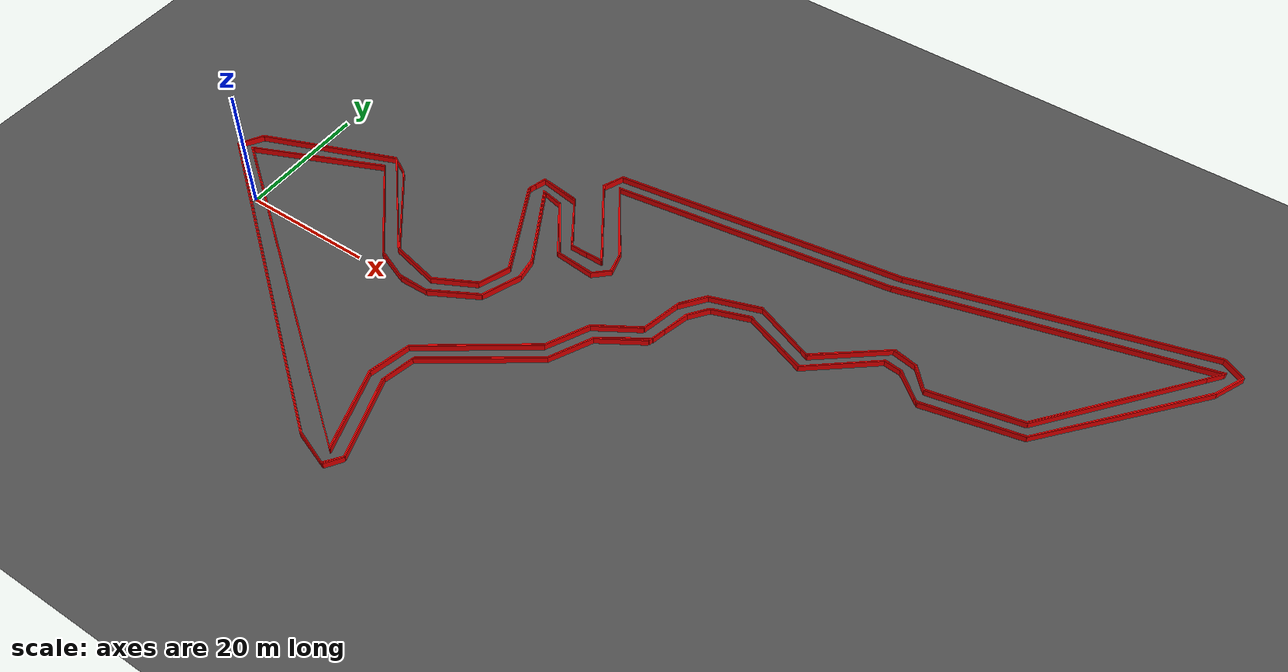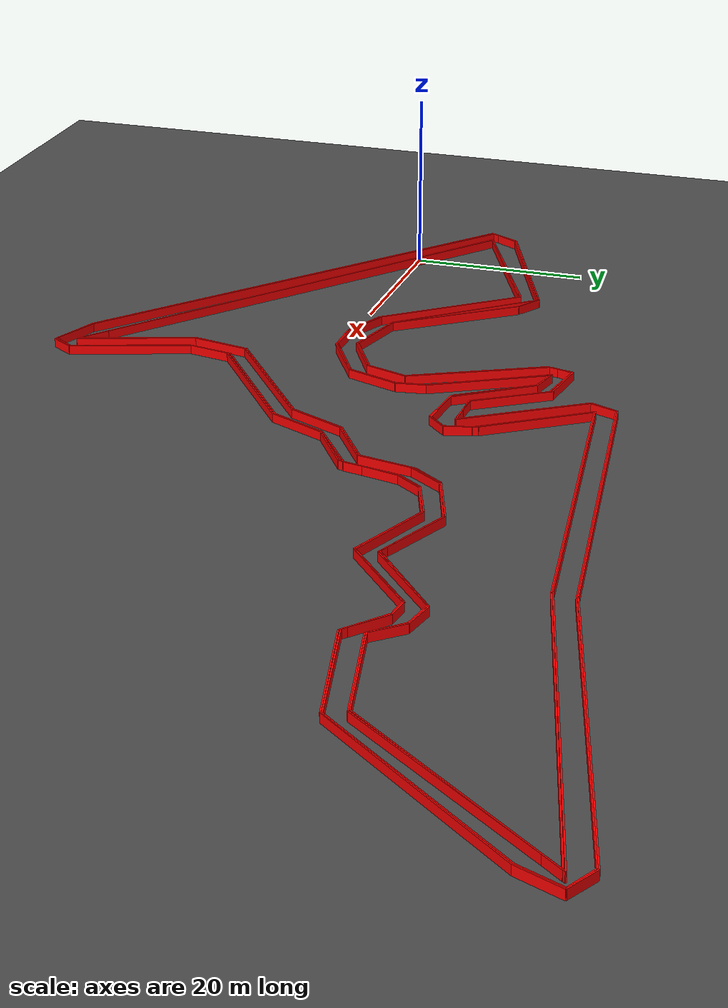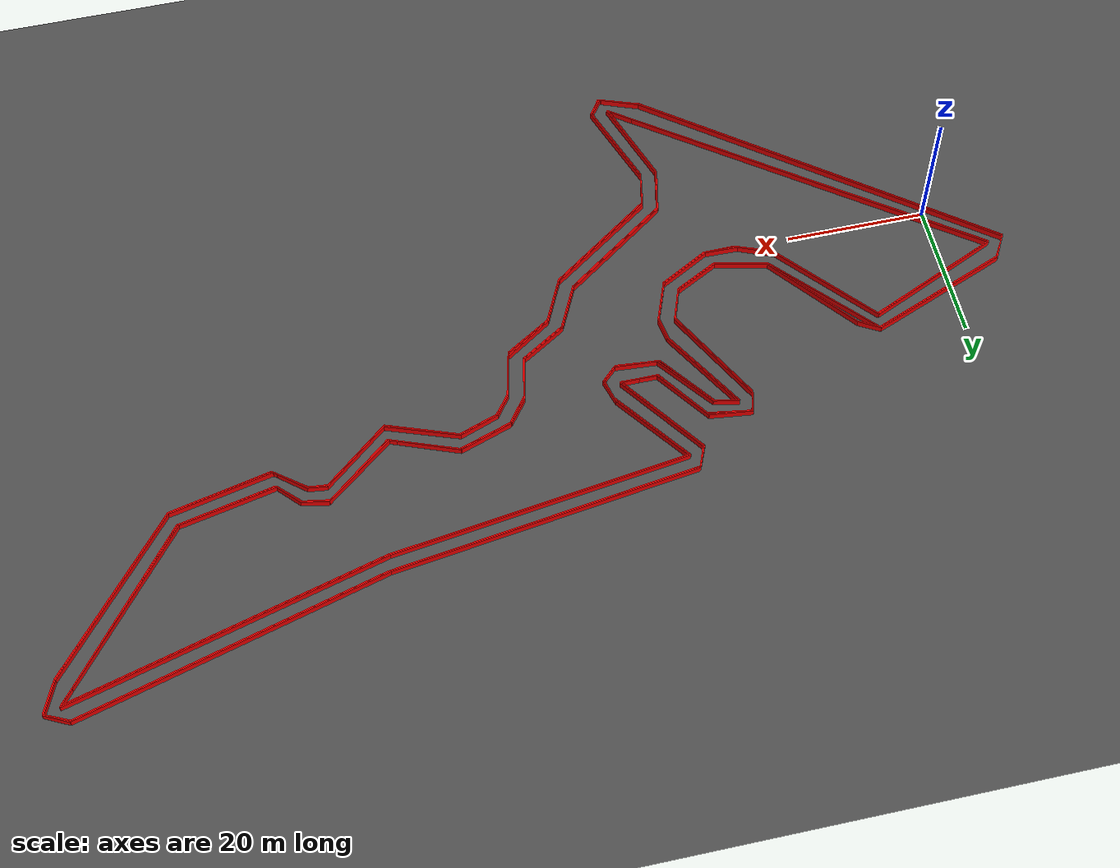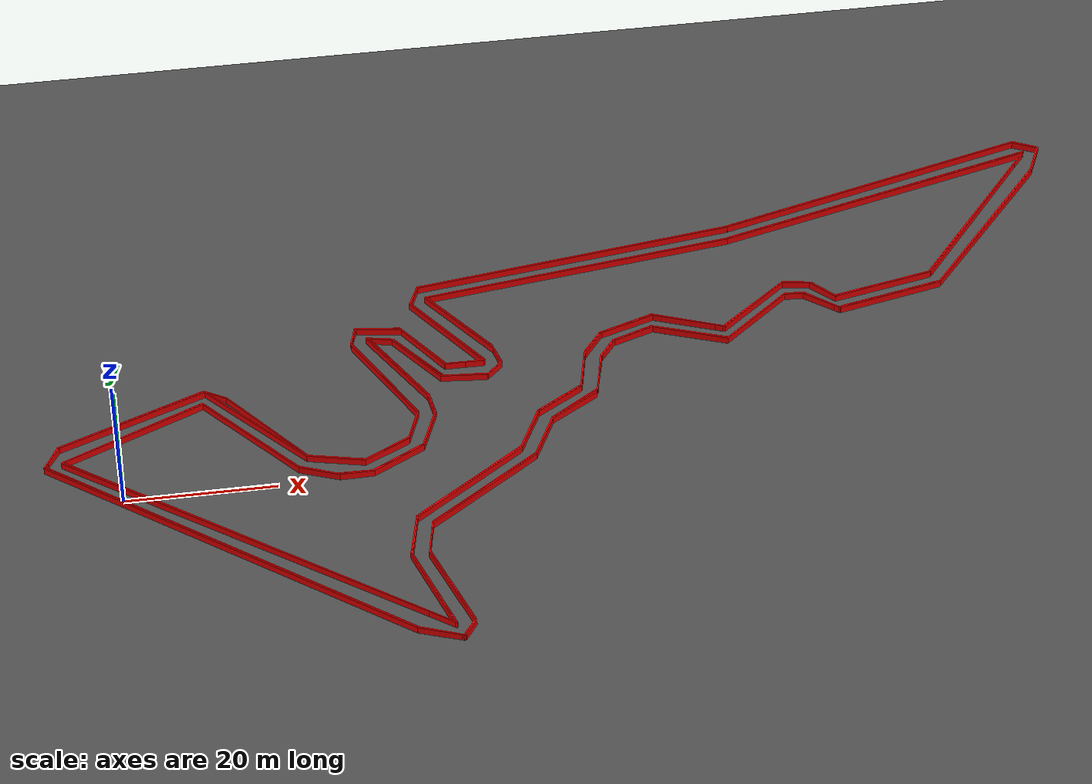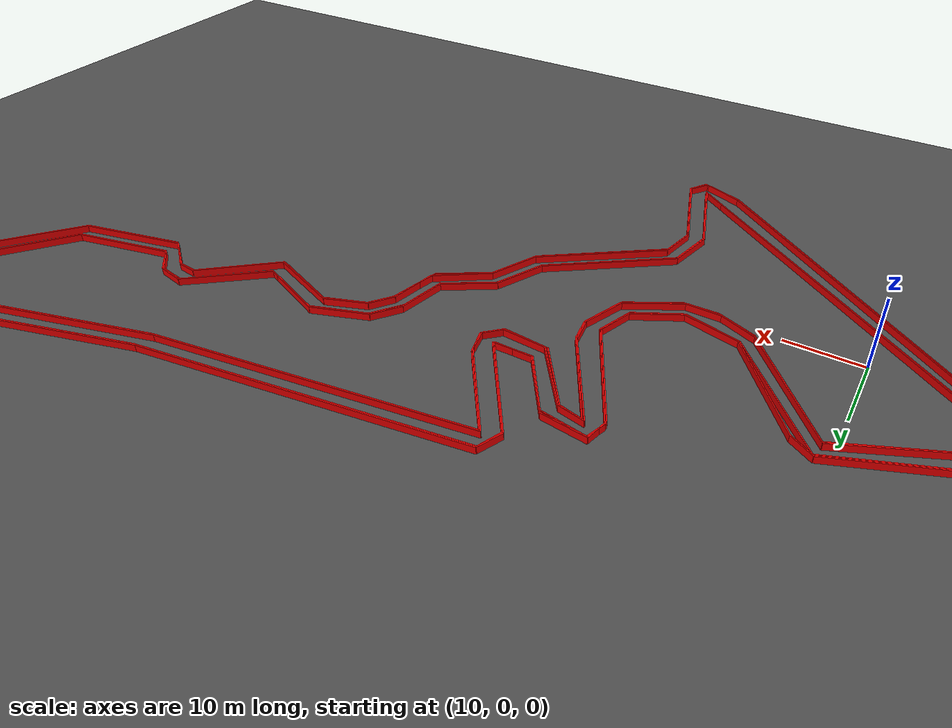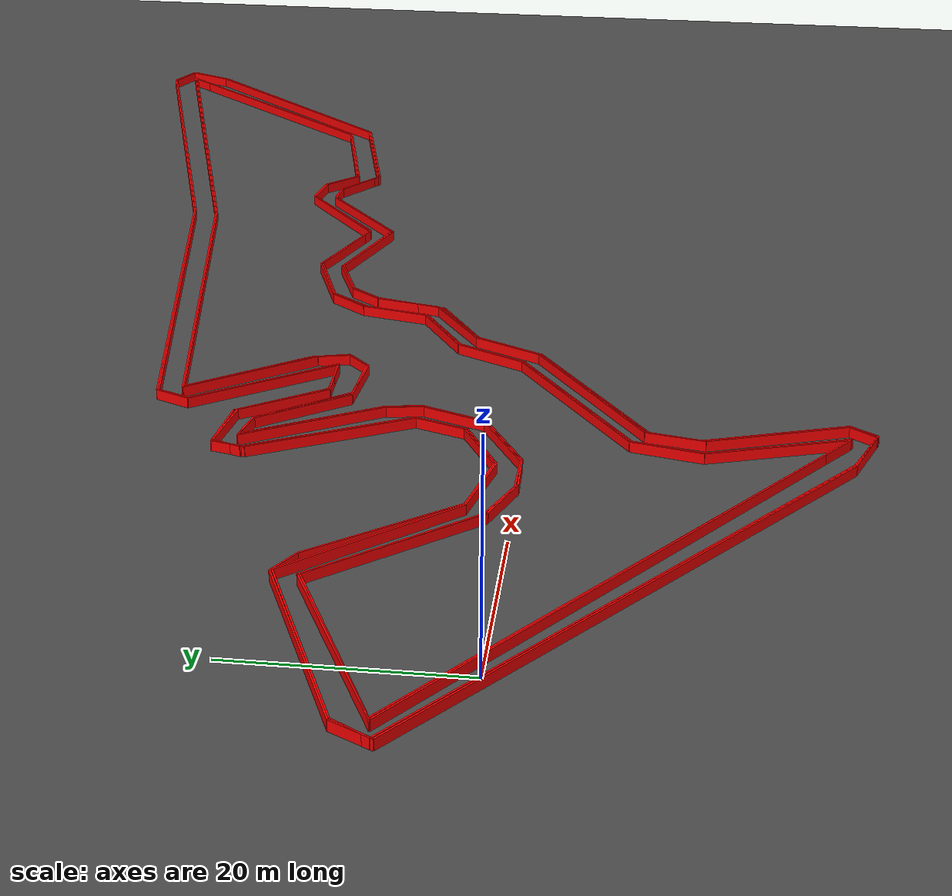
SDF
<?xml version="1.0" ?>
<sdf version="1.6">
  <world name="track_world">
    <scene>
      <ambient>0.4 0.4 0.4 1</ambient>
      <background>0.7 0.7 0.7 1</background>
      <shadows>true</shadows>
    </scene>
    <light name="sun" type="directional">
      <pose>0 0 10 0 0 0</pose>
      <diffuse>0.8 0.8 0.8 1</diffuse>
      <direction>-0.5 0.1 -0.9</direction>
    </light>
    <model name="ground_plane">
      <static>true</static>
      <link name="link">
        <collision name="collision">
          <geometry>
            <plane>
              <normal>0 0 1</normal>
              <size>1000 1000</size>
            </plane>
          </geometry>
        </collision>
        <visual name="visual">
          <geometry>
            <plane>
              <normal>0 0 1</normal>
              <size>1000 1000</size>
            </plane>
          </geometry>
          <material>
            <ambient>0.3 0.3 0.3 1</ambient>
            <diffuse>0.3 0.3 0.3 1</diffuse>
          </material>
        </visual>
      </link>
    </model>
    <model name="wall_0">
      <static>true</static>
      <pose>130.53235932739554 51.70391710065479 0.5 0 0 2.668236611754877</pose>
      <link name="link">
        <visual name="visual">
          <geometry>
            <box>
              <size>3.7262117004002757 0.15 1.0</size>
            </box>
          </geometry>
          <material>
            <ambient>1 0 0 1</ambient>
            <diffuse>1 0 0 1</diffuse>
          </material>
        </visual>
        <collision name="collision">
          <geometry>
            <box>
              <size>3.7262117004002757 0.15 1.0</size>
            </box>
          </geometry>
        </collision>
      </link>
    </model>
    <model name="wall_1">
      <static>true</static>
      <pose>107.23603932739553 46.52695710065479 0.5 0 0 -2.8699711045585703</pose>
      <link name="link">
        <visual name="visual">
          <geometry>
            <box>
              <size>44.92316291886182 0.15 1.0</size>
            </box>
          </geometry>
          <material>
            <ambient>1 0 0 1</ambient>
            <diffuse>1 0 0 1</diffuse>
          </material>
        </visual>
        <collision name="collision">
          <geometry>
            <box>
              <size>44.92316291886182 0.15 1.0</size>
            </box>
          </geometry>
        </collision>
      </link>
    </model>
    <model name="wall_2">
      <static>true</static>
      <pose>63.83855432739553 37.34594210065479 0.5 0 0 -2.9976144365376505</pose>
      <link name="link">
        <visual name="visual">
          <geometry>
            <box>
              <size>43.97381578767983 0.15 1.0</size>
            </box>
          </geometry>
          <material>
            <ambient>1 0 0 1</ambient>
            <diffuse>1 0 0 1</diffuse>
          </material>
        </visual>
        <collision name="collision">
          <geometry>
            <box>
              <size>43.97381578767983 0.15 1.0</size>
            </box>
          </geometry>
        </collision>
      </link>
    </model>
    <model name="wall_3">
      <static>true</static>
      <pose>41.391579327395526 32.61387710065479 0.5 0 0 -1.9818608741847612</pose>
      <link name="link">
        <visual name="visual">
          <geometry>
            <box>
              <size>3.441391826136623 0.15 1.0</size>
            </box>
          </geometry>
          <material>
            <ambient>1 0 0 1</ambient>
            <diffuse>1 0 0 1</diffuse>
          </material>
        </visual>
        <collision name="collision">
          <geometry>
            <box>
              <size>3.441391826136623 0.15 1.0</size>
            </box>
          </geometry>
        </collision>
      </link>
    </model>
    <model name="wall_4">
      <static>true</static>
      <pose>44.99118432739552 24.84843710065479 0.5 0 0 -0.9649118738723891</pose>
      <link name="link">
        <visual name="visual">
          <geometry>
            <box>
              <size>15.056191095509512 0.15 1.0</size>
            </box>
          </geometry>
          <material>
            <ambient>1 0 0 1</ambient>
            <diffuse>1 0 0 1</diffuse>
          </material>
        </visual>
        <collision name="collision">
          <geometry>
            <box>
              <size>15.056191095509512 0.15 1.0</size>
            </box>
          </geometry>
        </collision>
      </link>
    </model>
    <model name="wall_5">
      <static>true</static>
      <pose>46.73031932739552 18.70079710065479 0.5 0 0 3.125720970598004</pose>
      <link name="link">
        <visual name="visual">
          <geometry>
            <box>
              <size>5.096711943694677 0.15 1.0</size>
            </box>
          </geometry>
          <material>
            <ambient>1 0 0 1</ambient>
            <diffuse>1 0 0 1</diffuse>
          </material>
        </visual>
        <collision name="collision">
          <geometry>
            <box>
              <size>5.096711943694677 0.15 1.0</size>
            </box>
          </geometry>
        </collision>
      </link>
    </model>
    <model name="wall_6">
      <static>true</static>
      <pose>41.51291432739552 22.583517100654788 0.5 0 0 2.177981229497524</pose>
      <link name="link">
        <visual name="visual">
          <geometry>
            <box>
              <size>9.35705367570904 0.15 1.0</size>
            </box>
          </geometry>
          <material>
            <ambient>1 0 0 1</ambient>
            <diffuse>1 0 0 1</diffuse>
          </material>
        </visual>
        <collision name="collision">
          <geometry>
            <box>
              <size>9.35705367570904 0.15 1.0</size>
            </box>
          </geometry>
        </collision>
      </link>
    </model>
    <model name="wall_7">
      <static>true</static>
      <pose>35.81016932739552 26.789797100654788 0.5 0 0 3.022163727571455</pose>
      <link name="link">
        <visual name="visual">
          <geometry>
            <box>
              <size>6.110274471952957 0.15 1.0</size>
            </box>
          </geometry>
          <material>
            <ambient>1 0 0 1</ambient>
            <diffuse>1 0 0 1</diffuse>
          </material>
        </visual>
        <collision name="collision">
          <geometry>
            <box>
              <size>6.110274471952957 0.15 1.0</size>
            </box>
          </geometry>
        </collision>
      </link>
    </model>
    <model name="wall_8">
      <static>true</static>
      <pose>32.41278932739552 25.616892100654788 0.5 0 0 -1.803353268599805</pose>
      <link name="link">
        <visual name="visual">
          <geometry>
            <box>
              <size>3.1588554814204435 0.15 1.0</size>
            </box>
          </geometry>
          <material>
            <ambient>1 0 0 1</ambient>
            <diffuse>1 0 0 1</diffuse>
          </material>
        </visual>
        <collision name="collision">
          <geometry>
            <box>
              <size>3.1588554814204435 0.15 1.0</size>
            </box>
          </geometry>
        </collision>
      </link>
    </model>
    <model name="wall_9">
      <static>true</static>
      <pose>35.688834327395526 17.082997100654786 0.5 0 0 -1.0910950511828357</pose>
      <link name="link">
        <visual name="visual">
          <geometry>
            <box>
              <size>15.774379619208487 0.15 1.0</size>
            </box>
          </geometry>
          <material>
            <ambient>1 0 0 1</ambient>
            <diffuse>1 0 0 1</diffuse>
          </material>
        </visual>
        <collision name="collision">
          <geometry>
            <box>
              <size>15.774379619208487 0.15 1.0</size>
            </box>
          </geometry>
        </collision>
      </link>
    </model>
    <model name="wall_10">
      <static>true</static>
      <pose>38.51998432739552 7.821092100654788 0.5 0 0 -1.9138202672155997</pose>
      <link name="link">
        <visual name="visual">
          <geometry>
            <box>
              <size>4.810065203882368 0.15 1.0</size>
            </box>
          </geometry>
          <material>
            <ambient>1 0 0 1</ambient>
            <diffuse>1 0 0 1</diffuse>
          </material>
        </visual>
        <collision name="collision">
          <geometry>
            <box>
              <size>4.810065203882368 0.15 1.0</size>
            </box>
          </geometry>
        </collision>
      </link>
    </model>
    <model name="wall_11">
      <static>true</static>
      <pose>34.677709327395526 3.9383721006547887 0.5 0 0 -2.651635327336064</pose>
      <link name="link">
        <visual name="visual">
          <geometry>
            <box>
              <size>6.875650000000001 0.15 1.0</size>
            </box>
          </geometry>
          <material>
            <ambient>1 0 0 1</ambient>
            <diffuse>1 0 0 1</diffuse>
          </material>
        </visual>
        <collision name="collision">
          <geometry>
            <box>
              <size>6.875650000000001 0.15 1.0</size>
            </box>
          </geometry>
        </collision>
      </link>
    </model>
    <model name="wall_12">
      <static>true</static>
      <pose>27.963839327395526 3.1699171006547857 0.5 0 0 2.9147938055359077</pose>
      <link name="link">
        <visual name="visual">
          <geometry>
            <box>
              <size>7.554450443030255 0.15 1.0</size>
            </box>
          </geometry>
          <material>
            <ambient>1 0 0 1</ambient>
            <diffuse>1 0 0 1</diffuse>
          </material>
        </visual>
        <collision name="collision">
          <geometry>
            <box>
              <size>7.554450443030255 0.15 1.0</size>
            </box>
          </geometry>
        </collision>
      </link>
    </model>
    <model name="wall_13">
      <static>true</static>
      <pose>19.470389327395523 10.12645710065479 0.5 0 0 2.2382262701173006</pose>
      <link name="link">
        <visual name="visual">
          <geometry>
            <box>
              <size>15.551510100315028 0.15 1.0</size>
            </box>
          </geometry>
          <material>
            <ambient>1 0 0 1</ambient>
            <diffuse>1 0 0 1</diffuse>
          </material>
        </visual>
        <collision name="collision">
          <geometry>
            <box>
              <size>15.551510100315028 0.15 1.0</size>
            </box>
          </geometry>
        </collision>
      </link>
    </model>
    <model name="wall_14">
      <static>true</static>
      <pose>13.201414327395522 17.082997100654794 0.5 0 0 2.6135182051634334</pose>
      <link name="link">
        <visual name="visual">
          <geometry>
            <box>
              <size>3.3712793829197816 0.15 1.0</size>
            </box>
          </geometry>
          <material>
            <ambient>1 0 0 1</ambient>
            <diffuse>1 0 0 1</diffuse>
          </material>
        </visual>
        <collision name="collision">
          <geometry>
            <box>
              <size>3.3712793829197816 0.15 1.0</size>
            </box>
          </geometry>
        </collision>
      </link>
    </model>
    <model name="wall_15">
      <static>true</static>
      <pose>1.9172593273955219 13.96873210065479 0.5 0 0 -2.7582514151842017</pose>
      <link name="link">
        <visual name="visual">
          <geometry>
            <box>
              <size>21.194569286524796 0.15 1.0</size>
            </box>
          </geometry>
          <material>
            <ambient>1 0 0 1</ambient>
            <diffuse>1 0 0 1</diffuse>
          </material>
        </visual>
        <collision name="collision">
          <geometry>
            <box>
              <size>21.194569286524796 0.15 1.0</size>
            </box>
          </geometry>
        </collision>
      </link>
    </model>
    <model name="wall_16">
      <static>true</static>
      <pose>-8.88155567260448 8.225542100654785 0.5 0 0 -2.070143048475026</pose>
      <link name="link">
        <visual name="visual">
          <geometry>
            <box>
              <size>4.054195179712003 0.15 1.0</size>
            </box>
          </geometry>
          <material>
            <ambient>1 0 0 1</ambient>
            <diffuse>1 0 0 1</diffuse>
          </material>
        </visual>
        <collision name="collision">
          <geometry>
            <box>
              <size>4.054195179712003 0.15 1.0</size>
            </box>
          </geometry>
        </collision>
      </link>
    </model>
    <model name="wall_17">
      <static>true</static>
      <pose>12.554294327395521 -10.904942899345215 0.5 0 0 -0.6589152461643664</pose>
      <link name="link">
        <visual name="visual">
          <geometry>
            <box>
              <size>56.678267121002385 0.15 1.0</size>
            </box>
          </geometry>
          <material>
            <ambient>1 0 0 1</ambient>
            <diffuse>1 0 0 1</diffuse>
          </material>
        </visual>
        <collision name="collision">
          <geometry>
            <box>
              <size>56.678267121002385 0.15 1.0</size>
            </box>
          </geometry>
        </collision>
      </link>
    </model>
    <model name="wall_18">
      <static>true</static>
      <pose>37.87286432739552 -29.307417899345214 0.5 0 0 -0.3465388644339422</pose>
      <link name="link">
        <visual name="visual">
          <geometry>
            <box>
              <size>6.192181013665544 0.15 1.0</size>
            </box>
          </geometry>
          <material>
            <ambient>1 0 0 1</ambient>
            <diffuse>1 0 0 1</diffuse>
          </material>
        </visual>
        <collision name="collision">
          <geometry>
            <box>
              <size>6.192181013665544 0.15 1.0</size>
            </box>
          </geometry>
        </collision>
      </link>
    </model>
    <model name="wall_19">
      <static>true</static>
      <pose>41.593804327395524 -29.145637899345214 0.5 0 0 0.982793723247329</pose>
      <link name="link">
        <visual name="visual">
          <geometry>
            <box>
              <size>2.916530426722826 0.15 1.0</size>
            </box>
          </geometry>
          <material>
            <ambient>1 0 0 1</ambient>
            <diffuse>1 0 0 1</diffuse>
          </material>
        </visual>
        <collision name="collision">
          <geometry>
            <box>
              <size>2.916530426722826 0.15 1.0</size>
            </box>
          </geometry>
        </collision>
      </link>
    </model>
    <model name="wall_20">
      <static>true</static>
      <pose>40.218674327395526 -21.541977899345213 0.5 0 0 1.9001224938427344</pose>
      <link name="link">
        <visual name="visual">
          <geometry>
            <box>
              <size>13.506450153463714 0.15 1.0</size>
            </box>
          </geometry>
          <material>
            <ambient>1 0 0 1</ambient>
            <diffuse>1 0 0 1</diffuse>
          </material>
        </visual>
        <collision name="collision">
          <geometry>
            <box>
              <size>13.506450153463714 0.15 1.0</size>
            </box>
          </geometry>
        </collision>
      </link>
    </model>
    <model name="wall_21">
      <static>true</static>
      <pose>38.51998432739552 -12.805857899345213 0.5 0 0 1.3667783472023491</pose>
      <link name="link">
        <visual name="visual">
          <geometry>
            <box>
              <size>4.790982977093531 0.15 1.0</size>
            </box>
          </geometry>
          <material>
            <ambient>1 0 0 1</ambient>
            <diffuse>1 0 0 1</diffuse>
          </material>
        </visual>
        <collision name="collision">
          <geometry>
            <box>
              <size>4.790982977093531 0.15 1.0</size>
            </box>
          </geometry>
        </collision>
      </link>
    </model>
    <model name="wall_22">
      <static>true</static>
      <pose>46.40675932739552 -5.16175289934521 0.5 0 0 0.6212825434665654</pose>
      <link name="link">
        <visual name="visual">
          <geometry>
            <box>
              <size>18.204743334224744 0.15 1.0</size>
            </box>
          </geometry>
          <material>
            <ambient>1 0 0 1</ambient>
            <diffuse>1 0 0 1</diffuse>
          </material>
        </visual>
        <collision name="collision">
          <geometry>
            <box>
              <size>18.204743334224744 0.15 1.0</size>
            </box>
          </geometry>
        </collision>
      </link>
    </model>
    <model name="wall_23">
      <static>true</static>
      <pose>55.345104327395525 3.2912521006547877 0.5 0 0 1.1174576309403335</pose>
      <link name="link">
        <visual name="visual">
          <geometry>
            <box>
              <size>7.018343830904827 0.15 1.0</size>
            </box>
          </geometry>
          <material>
            <ambient>1 0 0 1</ambient>
            <diffuse>1 0 0 1</diffuse>
          </material>
        </visual>
        <collision name="collision">
          <geometry>
            <box>
              <size>7.018343830904827 0.15 1.0</size>
            </box>
          </geometry>
        </collision>
      </link>
    </model>
    <model name="wall_24">
      <static>true</static>
      <pose>60.077169327395524 8.468212100654782 0.5 0 0 0.5642681888579317</pose>
      <link name="link">
        <visual name="visual">
          <geometry>
            <box>
              <size>7.562674272114329 0.15 1.0</size>
            </box>
          </geometry>
          <material>
            <ambient>1 0 0 1</ambient>
            <diffuse>1 0 0 1</diffuse>
          </material>
        </visual>
        <collision name="collision">
          <geometry>
            <box>
              <size>7.562674272114329 0.15 1.0</size>
            </box>
          </geometry>
        </collision>
      </link>
    </model>
    <model name="wall_25">
      <static>true</static>
      <pose>64.12166932739552 13.887842100654787 0.5 0 0 1.325817663668033</pose>
      <link name="link">
        <visual name="visual">
          <geometry>
            <box>
              <size>7.003878295180474 0.15 1.0</size>
            </box>
          </geometry>
          <material>
            <ambient>1 0 0 1</ambient>
            <diffuse>1 0 0 1</diffuse>
          </material>
        </visual>
        <collision name="collision">
          <geometry>
            <box>
              <size>7.003878295180474 0.15 1.0</size>
            </box>
          </geometry>
        </collision>
      </link>
    </model>
    <model name="wall_26">
      <static>true</static>
      <pose>66.02258432739552 18.66035210065479 0.5 0 0 0.9179496956941228</pose>
      <link name="link">
        <visual name="visual">
          <geometry>
            <box>
              <size>3.462243192960305 0.15 1.0</size>
            </box>
          </geometry>
          <material>
            <ambient>1 0 0 1</ambient>
            <diffuse>1 0 0 1</diffuse>
          </material>
        </visual>
        <collision name="collision">
          <geometry>
            <box>
              <size>3.462243192960305 0.15 1.0</size>
            </box>
          </geometry>
        </collision>
      </link>
    </model>
    <model name="wall_27">
      <static>true</static>
      <pose>69.82441432739552 21.00616210065479 0.5 0 0 0.3392926144540447</pose>
      <link name="link">
        <visual name="visual">
          <geometry>
            <box>
              <size>5.833060853445652 0.15 1.0</size>
            </box>
          </geometry>
          <material>
            <ambient>1 0 0 1</ambient>
            <diffuse>1 0 0 1</diffuse>
          </material>
        </visual>
        <collision name="collision">
          <geometry>
            <box>
              <size>5.833060853445652 0.15 1.0</size>
            </box>
          </geometry>
        </collision>
      </link>
    </model>
    <model name="wall_28">
      <static>true</static>
      <pose>77.42807432739554 20.15681710065479 0.5 0 0 -0.35877067027057236</pose>
      <link name="link">
        <visual name="visual">
          <geometry>
            <box>
              <size>10.366866944381028 0.15 1.0</size>
            </box>
          </geometry>
          <material>
            <ambient>1 0 0 1</ambient>
            <diffuse>1 0 0 1</diffuse>
          </material>
        </visual>
        <collision name="collision">
          <geometry>
            <box>
              <size>10.366866944381028 0.15 1.0</size>
            </box>
          </geometry>
        </collision>
      </link>
    </model>
    <model name="wall_29">
      <static>true</static>
      <pose>86.81131432739554 22.098177100654787 0.5 0 0 0.6929792630592815</pose>
      <link name="link">
        <visual name="visual">
          <geometry>
            <box>
              <size>11.775817176540231 0.15 1.0</size>
            </box>
          </geometry>
          <material>
            <ambient>1 0 0 1</ambient>
            <diffuse>1 0 0 1</diffuse>
          </material>
        </visual>
        <collision name="collision">
          <geometry>
            <box>
              <size>11.775817176540231 0.15 1.0</size>
            </box>
          </geometry>
        </collision>
      </link>
    </model>
    <model name="wall_30">
      <static>true</static>
      <pose>92.63539432739552 25.73822710065479 0.5 0 0 -0.09347678115858589</pose>
      <link name="link">
        <visual name="visual">
          <geometry>
            <box>
              <size>2.5998302712484795 0.15 1.0</size>
            </box>
          </geometry>
          <material>
            <ambient>1 0 0 1</ambient>
            <diffuse>1 0 0 1</diffuse>
          </material>
        </visual>
        <collision name="collision">
          <geometry>
            <box>
              <size>2.5998302712484795 0.15 1.0</size>
            </box>
          </geometry>
        </collision>
      </link>
    </model>
    <model name="wall_31">
      <static>true</static>
      <pose>96.15410932739553 23.87775710065479 0.5 0 0 -0.6635557263775312</pose>
      <link name="link">
        <visual name="visual">
          <geometry>
            <box>
              <size>5.647257590671791 0.15 1.0</size>
            </box>
          </geometry>
          <material>
            <ambient>1 0 0 1</ambient>
            <diffuse>1 0 0 1</diffuse>
          </material>
        </visual>
        <collision name="collision">
          <geometry>
            <box>
              <size>5.647257590671791 0.15 1.0</size>
            </box>
          </geometry>
        </collision>
      </link>
    </model>
    <model name="wall_32">
      <static>true</static>
      <pose>105.57779432739552 23.756422100654788 0.5 0 0 0.22104706267501925</pose>
      <link name="link">
        <visual name="visual">
          <geometry>
            <box>
              <size>14.757493210447352 0.15 1.0</size>
            </box>
          </geometry>
          <material>
            <ambient>1 0 0 1</ambient>
            <diffuse>1 0 0 1</diffuse>
          </material>
        </visual>
        <collision name="collision">
          <geometry>
            <box>
              <size>14.757493210447352 0.15 1.0</size>
            </box>
          </geometry>
        </collision>
      </link>
    </model>
    <model name="wall_33">
      <static>true</static>
      <pose>121.47267932739553 35.80903210065479 0.5 0 0 0.8760580505981925</pose>
      <link name="link">
        <visual name="visual">
          <geometry>
            <box>
              <size>27.166157140215855 0.15 1.0</size>
            </box>
          </geometry>
          <material>
            <ambient>1 0 0 1</ambient>
            <diffuse>1 0 0 1</diffuse>
          </material>
        </visual>
        <collision name="collision">
          <geometry>
            <box>
              <size>27.166157140215855 0.15 1.0</size>
            </box>
          </geometry>
        </collision>
      </link>
    </model>
    <model name="wall_34">
      <static>true</static>
      <pose>131.17947932739554 48.54920710065479 0.5 0 0 1.1574659222555717</pose>
      <link name="link">
        <visual name="visual">
          <geometry>
            <box>
              <size>5.034712126368297 0.15 1.0</size>
            </box>
          </geometry>
          <material>
            <ambient>1 0 0 1</ambient>
            <diffuse>1 0 0 1</diffuse>
          </material>
        </visual>
        <collision name="collision">
          <geometry>
            <box>
              <size>5.034712126368297 0.15 1.0</size>
            </box>
          </geometry>
        </collision>
      </link>
    </model>
    <model name="wall_35">
      <static>true</static>
      <pose>131.05814432739552 48.630097100654794 0.5 0 0 -1.9822525702085945</pose>
      <link name="link">
        <visual name="visual">
          <geometry>
            <box>
              <size>4.854074036528478 0.15 1.0</size>
            </box>
          </geometry>
          <material>
            <ambient>1 0 0 1</ambient>
            <diffuse>1 0 0 1</diffuse>
          </material>
        </visual>
        <collision name="collision">
          <geometry>
            <box>
              <size>4.854074036528478 0.15 1.0</size>
            </box>
          </geometry>
        </collision>
      </link>
    </model>
    <model name="wall_36">
      <static>true</static>
      <pose>121.43223432739552 35.97081210065479 0.5 0 0 -2.2632427811829285</pose>
      <link name="link">
        <visual name="visual">
          <geometry>
            <box>
              <size>27.114443832688167 0.15 1.0</size>
            </box>
          </geometry>
          <material>
            <ambient>1 0 0 1</ambient>
            <diffuse>1 0 0 1</diffuse>
          </material>
        </visual>
        <collision name="collision">
          <geometry>
            <box>
              <size>27.114443832688167 0.15 1.0</size>
            </box>
          </geometry>
        </collision>
      </link>
    </model>
    <model name="wall_37">
      <static>true</static>
      <pose>105.45645932739552 23.91820210065479 0.5 0 0 -2.924093982196233</pose>
      <link name="link">
        <visual name="visual">
          <geometry>
            <box>
              <size>14.994353062006367 0.15 1.0</size>
            </box>
          </geometry>
          <material>
            <ambient>1 0 0 1</ambient>
            <diffuse>1 0 0 1</diffuse>
          </material>
        </visual>
        <collision name="collision">
          <geometry>
            <box>
              <size>14.994353062006367 0.15 1.0</size>
            </box>
          </geometry>
        </collision>
      </link>
    </model>
    <model name="wall_38">
      <static>true</static>
      <pose>96.11366432739553 23.999092100654792 0.5 0 0 2.4429328288683303</pose>
      <link name="link">
        <visual name="visual">
          <geometry>
            <box>
              <size>5.282061256214281 0.15 1.0</size>
            </box>
          </geometry>
          <material>
            <ambient>1 0 0 1</ambient>
            <diffuse>1 0 0 1</diffuse>
          </material>
        </visual>
        <collision name="collision">
          <geometry>
            <box>
              <size>5.282061256214281 0.15 1.0</size>
            </box>
          </geometry>
        </collision>
      </link>
    </model>
    <model name="wall_39">
      <static>true</static>
      <pose>92.75672932739553 25.85956210065479 0.5 0 0 3.0209689850096906</pose>
      <link name="link">
        <visual name="visual">
          <geometry>
            <box>
              <size>2.6889081930218452 0.15 1.0</size>
            </box>
          </geometry>
          <material>
            <ambient>1 0 0 1</ambient>
            <diffuse>1 0 0 1</diffuse>
          </material>
        </visual>
        <collision name="collision">
          <geometry>
            <box>
              <size>2.6889081930218452 0.15 1.0</size>
            </box>
          </geometry>
        </collision>
      </link>
    </model>
    <model name="wall_40">
      <static>true</static>
      <pose>86.89220432739552 22.259957100654788 0.5 0 0 -2.448613390530511</pose>
      <link name="link">
        <visual name="visual">
          <geometry>
            <box>
              <size>11.775817176540238 0.15 1.0</size>
            </box>
          </geometry>
          <material>
            <ambient>1 0 0 1</ambient>
            <diffuse>1 0 0 1</diffuse>
          </material>
        </visual>
        <collision name="collision">
          <geometry>
            <box>
              <size>11.775817176540238 0.15 1.0</size>
            </box>
          </geometry>
        </collision>
      </link>
    </model>
    <model name="wall_41">
      <static>true</static>
      <pose>77.38762932739553 20.318597100654785 0.5 0 0 2.7908647053415896</pose>
      <link name="link">
        <visual name="visual">
          <geometry>
            <box>
              <size>10.594428596361396 0.15 1.0</size>
            </box>
          </geometry>
          <material>
            <ambient>1 0 0 1</ambient>
            <diffuse>1 0 0 1</diffuse>
          </material>
        </visual>
        <collision name="collision">
          <geometry>
            <box>
              <size>10.594428596361396 0.15 1.0</size>
            </box>
          </geometry>
        </collision>
      </link>
    </model>
    <model name="wall_42">
      <static>true</static>
      <pose>69.66263432739552 21.127497100654786 0.5 0 0 -2.7892839289156512</pose>
      <link name="link">
        <visual name="visual">
          <geometry>
            <box>
              <size>5.860479104382161 0.15 1.0</size>
            </box>
          </geometry>
          <material>
            <ambient>1 0 0 1</ambient>
            <diffuse>1 0 0 1</diffuse>
          </material>
        </visual>
        <collision name="collision">
          <geometry>
            <box>
              <size>5.860479104382161 0.15 1.0</size>
            </box>
          </geometry>
        </collision>
      </link>
    </model>
    <model name="wall_43">
      <static>true</static>
      <pose>65.86080432739553 18.70079710065479 0.5 0 0 -2.209710311798784</pose>
      <link name="link">
        <visual name="visual">
          <geometry>
            <box>
              <size>3.5268411053093884 0.15 1.0</size>
            </box>
          </geometry>
          <material>
            <ambient>1 0 0 1</ambient>
            <diffuse>1 0 0 1</diffuse>
          </material>
        </visual>
        <collision name="collision">
          <geometry>
            <box>
              <size>3.5268411053093884 0.15 1.0</size>
            </box>
          </geometry>
        </collision>
      </link>
    </model>
    <model name="wall_44">
      <static>true</static>
      <pose>64.16211432739553 14.211402100654787 0.5 0 0 -1.7782925532300993</pose>
      <link name="link">
        <visual name="visual">
          <geometry>
            <box>
              <size>6.282398805169895 0.15 1.0</size>
            </box>
          </geometry>
          <material>
            <ambient>1 0 0 1</ambient>
            <diffuse>1 0 0 1</diffuse>
          </material>
        </visual>
        <collision name="collision">
          <geometry>
            <box>
              <size>6.282398805169895 0.15 1.0</size>
            </box>
          </geometry>
        </collision>
      </link>
    </model>
    <model name="wall_45">
      <static>true</static>
      <pose>60.15805932739553 8.872662100654786 0.5 0 0 -2.5480499405184522</pose>
      <link name="link">
        <visual name="visual">
          <geometry>
            <box>
              <size>8.09910493835584 0.15 1.0</size>
            </box>
          </geometry>
          <material>
            <ambient>1 0 0 1</ambient>
            <diffuse>1 0 0 1</diffuse>
          </material>
        </visual>
        <collision name="collision">
          <geometry>
            <box>
              <size>8.09910493835584 0.15 1.0</size>
            </box>
          </geometry>
        </collision>
      </link>
    </model>
    <model name="wall_46">
      <static>true</static>
      <pose>55.30465932739553 3.4934771006547862 0.5 0 0 -2.018738420964563</pose>
      <link name="link">
        <visual name="visual">
          <geometry>
            <box>
              <size>6.910297818893198 0.15 1.0</size>
            </box>
          </geometry>
          <material>
            <ambient>1 0 0 1</ambient>
            <diffuse>1 0 0 1</diffuse>
          </material>
        </visual>
        <collision name="collision">
          <geometry>
            <box>
              <size>6.910297818893198 0.15 1.0</size>
            </box>
          </geometry>
        </collision>
      </link>
    </model>
    <model name="wall_47">
      <static>true</static>
      <pose>46.40675932739552 -4.878637899345215 0.5 0 0 -2.5239324937725054</pose>
      <link name="link">
        <visual name="visual">
          <geometry>
            <box>
              <size>18.15777813299028 0.15 1.0</size>
            </box>
          </geometry>
          <material>
            <ambient>1 0 0 1</ambient>
            <diffuse>1 0 0 1</diffuse>
          </material>
        </visual>
        <collision name="collision">
          <geometry>
            <box>
              <size>18.15777813299028 0.15 1.0</size>
            </box>
          </geometry>
        </collision>
      </link>
    </model>
    <model name="wall_48">
      <static>true</static>
      <pose>38.47953932739552 -12.805857899345213 0.5 0 0 -1.7652764430100019</pose>
      <link name="link">
        <visual name="visual">
          <geometry>
            <box>
              <size>5.441318245838963 0.15 1.0</size>
            </box>
          </geometry>
          <material>
            <ambient>1 0 0 1</ambient>
            <diffuse>1 0 0 1</diffuse>
          </material>
        </visual>
        <collision name="collision">
          <geometry>
            <box>
              <size>5.441318245838963 0.15 1.0</size>
            </box>
          </geometry>
        </collision>
      </link>
    </model>
    <model name="wall_49">
      <static>true</static>
      <pose>40.097339327395524 -21.703757899345213 0.5 0 0 -1.2393373395641452</pose>
      <link name="link">
        <visual name="visual">
          <geometry>
            <box>
              <size>13.174147807448495 0.15 1.0</size>
            </box>
          </geometry>
          <material>
            <ambient>1 0 0 1</ambient>
            <diffuse>1 0 0 1</diffuse>
          </material>
        </visual>
        <collision name="collision">
          <geometry>
            <box>
              <size>13.174147807448495 0.15 1.0</size>
            </box>
          </geometry>
        </collision>
      </link>
    </model>
    <model name="wall_50">
      <static>true</static>
      <pose>41.391579327395526 -29.105192899345212 0.5 0 0 -2.1975392280059434</pose>
      <link name="link">
        <visual name="visual">
          <geometry>
            <box>
              <size>2.896268680941048 0.15 1.0</size>
            </box>
          </geometry>
          <material>
            <ambient>1 0 0 1</ambient>
            <diffuse>1 0 0 1</diffuse>
          </material>
        </visual>
        <collision name="collision">
          <geometry>
            <box>
              <size>2.896268680941048 0.15 1.0</size>
            </box>
          </geometry>
        </collision>
      </link>
    </model>
    <model name="wall_51">
      <static>true</static>
      <pose>37.83241932739553 -29.226527899345214 0.5 0 0 2.7714218257475776</pose>
      <link name="link">
        <visual name="visual">
          <geometry>
            <box>
              <size>5.813397216473345 0.15 1.0</size>
            </box>
          </geometry>
          <material>
            <ambient>1 0 0 1</ambient>
            <diffuse>1 0 0 1</diffuse>
          </material>
        </visual>
        <collision name="collision">
          <geometry>
            <box>
              <size>5.813397216473345 0.15 1.0</size>
            </box>
          </geometry>
        </collision>
      </link>
    </model>
    <model name="wall_52">
      <static>true</static>
      <pose>12.675629327395521 -10.743162899345215 0.5 0 0 2.481298361284085</pose>
      <link name="link">
        <visual name="visual">
          <geometry>
            <box>
              <size>56.841328751979404 0.15 1.0</size>
            </box>
          </geometry>
          <material>
            <ambient>1 0 0 1</ambient>
            <diffuse>1 0 0 1</diffuse>
          </material>
        </visual>
        <collision name="collision">
          <geometry>
            <box>
              <size>56.841328751979404 0.15 1.0</size>
            </box>
          </geometry>
        </collision>
      </link>
    </model>
    <model name="wall_53">
      <static>true</static>
      <pose>-8.76022067260448 8.306432100654789 0.5 0 0 1.012197011451335</pose>
      <link name="link">
        <visual name="visual">
          <geometry>
            <box>
              <size>3.8155736688602975 0.15 1.0</size>
            </box>
          </geometry>
          <material>
            <ambient>1 0 0 1</ambient>
            <diffuse>1 0 0 1</diffuse>
          </material>
        </visual>
        <collision name="collision">
          <geometry>
            <box>
              <size>3.8155736688602975 0.15 1.0</size>
            </box>
          </geometry>
        </collision>
      </link>
    </model>
    <model name="wall_54">
      <static>true</static>
      <pose>2.079039327395522 13.847397100654788 0.5 0 0 0.37979665402357987</pose>
      <link name="link">
        <visual name="visual">
          <geometry>
            <box>
              <size>21.164447660683233 0.15 1.0</size>
            </box>
          </geometry>
          <material>
            <ambient>1 0 0 1</ambient>
            <diffuse>1 0 0 1</diffuse>
          </material>
        </visual>
        <collision name="collision">
          <geometry>
            <box>
              <size>21.164447660683233 0.15 1.0</size>
            </box>
          </geometry>
        </collision>
      </link>
    </model>
    <model name="wall_55">
      <static>true</static>
      <pose>18.014369327395524 10.854467100654787 0.5 0 0 -0.8474302758102056</pose>
      <link name="link">
        <visual name="visual">
          <geometry>
            <box>
              <size>18.453205772119922 0.15 1.0</size>
            </box>
          </geometry>
          <material>
            <ambient>1 0 0 1</ambient>
            <diffuse>1 0 0 1</diffuse>
          </material>
        </visual>
        <collision name="collision">
          <geometry>
            <box>
              <size>18.453205772119922 0.15 1.0</size>
            </box>
          </geometry>
        </collision>
      </link>
    </model>
    <model name="wall_56">
      <static>true</static>
      <pose>27.882949327395526 3.048582100654791 0.5 0 0 -0.23228898897102124</pose>
      <link name="link">
        <visual name="visual">
          <geometry>
            <box>
              <size>7.730392839261146 0.15 1.0</size>
            </box>
          </geometry>
          <material>
            <ambient>1 0 0 1</ambient>
            <diffuse>1 0 0 1</diffuse>
          </material>
        </visual>
        <collision name="collision">
          <geometry>
            <box>
              <size>7.730392839261146 0.15 1.0</size>
            </box>
          </geometry>
        </collision>
      </link>
    </model>
    <model name="wall_57">
      <static>true</static>
      <pose>34.677709327395526 3.73614710065479 0.5 0 0 0.4795192919925955</pose>
      <link name="link">
        <visual name="visual">
          <geometry>
            <box>
              <size>6.837956620701827 0.15 1.0</size>
            </box>
          </geometry>
          <material>
            <ambient>1 0 0 1</ambient>
            <diffuse>1 0 0 1</diffuse>
          </material>
        </visual>
        <collision name="collision">
          <geometry>
            <box>
              <size>6.837956620701827 0.15 1.0</size>
            </box>
          </geometry>
        </collision>
      </link>
    </model>
    <model name="wall_58">
      <static>true</static>
      <pose>38.60087432739552 7.740202100654784 0.5 0 0 1.2193515327913453</pose>
      <link name="link">
        <visual name="visual">
          <geometry>
            <box>
              <size>5.169371000073405 0.15 1.0</size>
            </box>
          </geometry>
          <material>
            <ambient>1 0 0 1</ambient>
            <diffuse>1 0 0 1</diffuse>
          </material>
        </visual>
        <collision name="collision">
          <geometry>
            <box>
              <size>5.169371000073405 0.15 1.0</size>
            </box>
          </geometry>
        </collision>
      </link>
    </model>
    <model name="wall_59">
      <static>true</static>
      <pose>35.76972432739552 17.325667100654783 0.5 0 0 2.050137714501876</pose>
      <link name="link">
        <visual name="visual">
          <geometry>
            <box>
              <size>16.136085127294667 0.15 1.0</size>
            </box>
          </geometry>
          <material>
            <ambient>1 0 0 1</ambient>
            <diffuse>1 0 0 1</diffuse>
          </material>
        </visual>
        <collision name="collision">
          <geometry>
            <box>
              <size>16.136085127294667 0.15 1.0</size>
            </box>
          </geometry>
        </collision>
      </link>
    </model>
    <model name="wall_60">
      <static>true</static>
      <pose>32.493679327395526 25.778672100654788 0.5 0 0 1.2397002500907657</pose>
      <link name="link">
        <visual name="visual">
          <geometry>
            <box>
              <size>2.7371435757921097 0.15 1.0</size>
            </box>
          </geometry>
          <material>
            <ambient>1 0 0 1</ambient>
            <diffuse>1 0 0 1</diffuse>
          </material>
        </visual>
        <collision name="collision">
          <geometry>
            <box>
              <size>2.7371435757921097 0.15 1.0</size>
            </box>
          </geometry>
        </collision>
      </link>
    </model>
    <model name="wall_61">
      <static>true</static>
      <pose>35.97194932739552 26.58757210065479 0.5 0 0 -0.1586552621864017</pose>
      <link name="link">
        <visual name="visual">
          <geometry>
            <box>
              <size>6.143913673294897 0.15 1.0</size>
            </box>
          </geometry>
          <material>
            <ambient>1 0 0 1</ambient>
            <diffuse>1 0 0 1</diffuse>
          </material>
        </visual>
        <collision name="collision">
          <geometry>
            <box>
              <size>6.143913673294897 0.15 1.0</size>
            </box>
          </geometry>
        </collision>
      </link>
    </model>
    <model name="wall_62">
      <static>true</static>
      <pose>41.51291432739552 22.38129210065479 0.5 0 0 -0.9777937649133699</pose>
      <link name="link">
        <visual name="visual">
          <geometry>
            <box>
              <size>8.97405194807786 0.15 1.0</size>
            </box>
          </geometry>
          <material>
            <ambient>1 0 0 1</ambient>
            <diffuse>1 0 0 1</diffuse>
          </material>
        </visual>
        <collision name="collision">
          <geometry>
            <box>
              <size>8.97405194807786 0.15 1.0</size>
            </box>
          </geometry>
        </collision>
      </link>
    </model>
    <model name="wall_63">
      <static>true</static>
      <pose>46.73031932739553 18.70079710065479 0.5 0 0 0.014924264990084361</pose>
      <link name="link">
        <visual name="visual">
          <geometry>
            <box>
              <size>5.420233623101497 0.15 1.0</size>
            </box>
          </geometry>
          <material>
            <ambient>1 0 0 1</ambient>
            <diffuse>1 0 0 1</diffuse>
          </material>
        </visual>
        <collision name="collision">
          <geometry>
            <box>
              <size>5.420233623101497 0.15 1.0</size>
            </box>
          </geometry>
        </collision>
      </link>
    </model>
    <model name="wall_64">
      <static>true</static>
      <pose>45.15296432739552 24.88888210065479 0.5 0 0 2.179753946431405</pose>
      <link name="link">
        <visual name="visual">
          <geometry>
            <box>
              <size>14.989770402311045 0.15 1.0</size>
            </box>
          </geometry>
          <material>
            <ambient>1 0 0 1</ambient>
            <diffuse>1 0 0 1</diffuse>
          </material>
        </visual>
        <collision name="collision">
          <geometry>
            <box>
              <size>14.989770402311045 0.15 1.0</size>
            </box>
          </geometry>
        </collision>
      </link>
    </model>
    <model name="wall_65">
      <static>true</static>
      <pose>41.47246932739552 32.53298710065479 0.5 0 0 1.185638820431421</pose>
      <link name="link">
        <visual name="visual">
          <geometry>
            <box>
              <size>3.229527551732609 0.15 1.0</size>
            </box>
          </geometry>
          <material>
            <ambient>1 0 0 1</ambient>
            <diffuse>1 0 0 1</diffuse>
          </material>
        </visual>
        <collision name="collision">
          <geometry>
            <box>
              <size>3.229527551732609 0.15 1.0</size>
            </box>
          </geometry>
        </collision>
      </link>
    </model>
    <model name="wall_66">
      <static>true</static>
      <pose>64.00033432739554 37.224607100654794 0.5 0 0 0.14473722254184004</pose>
      <link name="link">
        <visual name="visual">
          <geometry>
            <box>
              <size>44.30564688570183 0.15 1.0</size>
            </box>
          </geometry>
          <material>
            <ambient>1 0 0 1</ambient>
            <diffuse>1 0 0 1</diffuse>
          </material>
        </visual>
        <collision name="collision">
          <geometry>
            <box>
              <size>44.30564688570183 0.15 1.0</size>
            </box>
          </geometry>
        </collision>
      </link>
    </model>
    <model name="wall_67">
      <static>true</static>
      <pose>107.35737432739553 46.40562210065479 0.5 0 0 0.27230871720075683</pose>
      <link name="link">
        <visual name="visual">
          <geometry>
            <box>
              <size>44.511849440889335 0.15 1.0</size>
            </box>
          </geometry>
          <material>
            <ambient>1 0 0 1</ambient>
            <diffuse>1 0 0 1</diffuse>
          </material>
        </visual>
        <collision name="collision">
          <geometry>
            <box>
              <size>44.511849440889335 0.15 1.0</size>
            </box>
          </geometry>
        </collision>
      </link>
    </model>
    <model name="wall_68">
      <static>true</static>
      <pose>130.41102432739552 51.62302710065479 0.5 0 0 -0.4434483364197389</pose>
      <link name="link">
        <visual name="visual">
          <geometry>
            <box>
              <size>3.5820664019668627 0.15 1.0</size>
            </box>
          </geometry>
          <material>
            <ambient>1 0 0 1</ambient>
            <diffuse>1 0 0 1</diffuse>
          </material>
        </visual>
        <collision name="collision">
          <geometry>
            <box>
              <size>3.5820664019668627 0.15 1.0</size>
            </box>
          </geometry>
        </collision>
      </link>
    </model>
    <model name="wall_69">
      <static>true</static>
      <pose>107.55959932739552 44.18114710065479 0.5 0 0 -2.8750346068963992</pose>
      <link name="link">
        <visual name="visual">
          <geometry>
            <box>
              <size>46.36980004249533 0.15 1.0</size>
            </box>
          </geometry>
          <material>
            <ambient>1 0 0 1</ambient>
            <diffuse>1 0 0 1</diffuse>
          </material>
        </visual>
        <collision name="collision">
          <geometry>
            <box>
              <size>46.36980004249533 0.15 1.0</size>
            </box>
          </geometry>
        </collision>
      </link>
    </model>
    <model name="wall_70">
      <static>true</static>
      <pose>64.04077932739551 35.040577100654794 0.5 0 0 -2.999160267130986</pose>
      <link name="link">
        <visual name="visual">
          <geometry>
            <box>
              <size>42.73825274251861 0.15 1.0</size>
            </box>
          </geometry>
          <material>
            <ambient>1 0 0 1</ambient>
            <diffuse>1 0 0 1</diffuse>
          </material>
        </visual>
        <collision name="collision">
          <geometry>
            <box>
              <size>42.73825274251861 0.15 1.0</size>
            </box>
          </geometry>
        </collision>
      </link>
    </model>
    <model name="wall_71">
      <static>true</static>
      <pose>46.85165432739552 26.466237100654794 0.5 0 0 -0.9498567097967265</pose>
      <link name="link">
        <visual name="visual">
          <geometry>
            <box>
              <size>13.625343645328732 0.15 1.0</size>
            </box>
          </geometry>
          <material>
            <ambient>1 0 0 1</ambient>
            <diffuse>1 0 0 1</diffuse>
          </material>
        </visual>
        <collision name="collision">
          <geometry>
            <box>
              <size>13.625343645328732 0.15 1.0</size>
            </box>
          </geometry>
        </collision>
      </link>
    </model>
    <model name="wall_72">
      <static>true</static>
      <pose>51.138824327395525 19.428807100654794 0.5 0 0 -1.3578579772154993</pose>
      <link name="link">
        <visual name="visual">
          <geometry>
            <box>
              <size>3.062089854870364 0.15 1.0</size>
            </box>
          </geometry>
          <material>
            <ambient>1 0 0 1</ambient>
            <diffuse>1 0 0 1</diffuse>
          </material>
        </visual>
        <collision name="collision">
          <geometry>
            <box>
              <size>3.062089854870364 0.15 1.0</size>
            </box>
          </geometry>
        </collision>
      </link>
    </model>
    <model name="wall_73">
      <static>true</static>
      <pose>50.491704327395524 17.00210710065479 0.5 0 0 -2.377467876216405</pose>
      <link name="link">
        <visual name="visual">
          <geometry>
            <box>
              <size>2.688908193021851 0.15 1.0</size>
            </box>
          </geometry>
          <material>
            <ambient>1 0 0 1</ambient>
            <diffuse>1 0 0 1</diffuse>
          </material>
        </visual>
        <collision name="collision">
          <geometry>
            <box>
              <size>2.688908193021851 0.15 1.0</size>
            </box>
          </geometry>
        </collision>
      </link>
    </model>
    <model name="wall_74">
      <static>true</static>
      <pose>46.56853932739552 16.274097100654785 0.5 0 0 3.07320630999929</pose>
      <link name="link">
        <visual name="visual">
          <geometry>
            <box>
              <size>5.918804820519094 0.15 1.0</size>
            </box>
          </geometry>
          <material>
            <ambient>1 0 0 1</ambient>
            <diffuse>1 0 0 1</diffuse>
          </material>
        </visual>
        <collision name="collision">
          <geometry>
            <box>
              <size>5.918804820519094 0.15 1.0</size>
            </box>
          </geometry>
        </collision>
      </link>
    </model>
    <model name="wall_75">
      <static>true</static>
      <pose>40.66356932739552 20.439932100654786 0.5 0 0 2.2110241248566695</pose>
      <link name="link">
        <visual name="visual">
          <geometry>
            <box>
              <size>9.884810955668296 0.15 1.0</size>
            </box>
          </geometry>
          <material>
            <ambient>1 0 0 1</ambient>
            <diffuse>1 0 0 1</diffuse>
          </material>
        </visual>
        <collision name="collision">
          <geometry>
            <box>
              <size>9.884810955668296 0.15 1.0</size>
            </box>
          </geometry>
        </collision>
      </link>
    </model>
    <model name="wall_76">
      <static>true</static>
      <pose>35.93150432739552 24.767547100654788 0.5 0 0 2.939830309269507</pose>
      <link name="link">
        <visual name="visual">
          <geometry>
            <box>
              <size>3.6328526622614405 0.15 1.0</size>
            </box>
          </geometry>
          <material>
            <ambient>1 0 0 1</ambient>
            <diffuse>1 0 0 1</diffuse>
          </material>
        </visual>
        <collision name="collision">
          <geometry>
            <box>
              <size>3.6328526622614405 0.15 1.0</size>
            </box>
          </geometry>
        </collision>
      </link>
    </model>
    <model name="wall_77">
      <static>true</static>
      <pose>37.63019432739552 19.105247100654786 0.5 0 0 -1.047324356330717</pose>
      <link name="link">
        <visual name="visual">
          <geometry>
            <box>
              <size>13.916136553788917 0.15 1.0</size>
            </box>
          </geometry>
          <material>
            <ambient>1 0 0 1</ambient>
            <diffuse>1 0 0 1</diffuse>
          </material>
        </visual>
        <collision name="collision">
          <geometry>
            <box>
              <size>13.916136553788917 0.15 1.0</size>
            </box>
          </geometry>
        </collision>
      </link>
    </model>
    <model name="wall_78">
      <static>true</static>
      <pose>41.35113432739553 11.380252100654786 0.5 0 0 -1.4288992721907323</pose>
      <link name="link">
        <visual name="visual">
          <geometry>
            <box>
              <size>3.4318720518107884 0.15 1.0</size>
            </box>
          </geometry>
          <material>
            <ambient>1 0 0 1</ambient>
            <diffuse>1 0 0 1</diffuse>
          </material>
        </visual>
        <collision name="collision">
          <geometry>
            <box>
              <size>3.4318720518107884 0.15 1.0</size>
            </box>
          </geometry>
        </collision>
      </link>
    </model>
    <model name="wall_79">
      <static>true</static>
      <pose>40.50178932739553 6.850412100654786 0.5 0 0 -1.9389270981200601</pose>
      <link name="link">
        <visual name="visual">
          <geometry>
            <box>
              <size>6.068906683324437 0.15 1.0</size>
            </box>
          </geometry>
          <material>
            <ambient>1 0 0 1</ambient>
            <diffuse>1 0 0 1</diffuse>
          </material>
        </visual>
        <collision name="collision">
          <geometry>
            <box>
              <size>6.068906683324437 0.15 1.0</size>
            </box>
          </geometry>
        </collision>
      </link>
    </model>
    <model name="wall_80">
      <static>true</static>
      <pose>35.891059327395524 2.0779021006547893 0.5 0 0 -2.6374266921106413</pose>
      <link name="link">
        <visual name="visual">
          <geometry>
            <box>
              <size>8.037470721769377 0.15 1.0</size>
            </box>
          </geometry>
          <material>
            <ambient>1 0 0 1</ambient>
            <diffuse>1 0 0 1</diffuse>
          </material>
        </visual>
        <collision name="collision">
          <geometry>
            <box>
              <size>8.037470721769377 0.15 1.0</size>
            </box>
          </geometry>
        </collision>
      </link>
    </model>
    <model name="wall_81">
      <static>true</static>
      <pose>30.026534327395524 0.17698710065479162 0.5 0 0 3.1243529823952643</pose>
      <link name="link">
        <visual name="visual">
          <geometry>
            <box>
              <size>4.692317275771109 0.15 1.0</size>
            </box>
          </geometry>
          <material>
            <ambient>1 0 0 1</ambient>
            <diffuse>1 0 0 1</diffuse>
          </material>
        </visual>
        <collision name="collision">
          <geometry>
            <box>
              <size>4.692317275771109 0.15 1.0</size>
            </box>
          </geometry>
        </collision>
      </link>
    </model>
    <model name="wall_82">
      <static>true</static>
      <pose>25.254024327395523 1.2285571006547897 0.5 0 0 2.746801533890032</pose>
      <link name="link">
        <visual name="visual">
          <geometry>
            <box>
              <size>5.25785 0.15 1.0</size>
            </box>
          </geometry>
          <material>
            <ambient>1 0 0 1</ambient>
            <diffuse>1 0 0 1</diffuse>
          </material>
        </visual>
        <collision name="collision">
          <geometry>
            <box>
              <size>5.25785 0.15 1.0</size>
            </box>
          </geometry>
        </collision>
      </link>
    </model>
    <model name="wall_83">
      <static>true</static>
      <pose>17.124579327395523 8.95355210065479 0.5 0 0 2.2749405572224544</pose>
      <link name="link">
        <visual name="visual">
          <geometry>
            <box>
              <size>17.617871711637022 0.15 1.0</size>
            </box>
          </geometry>
          <material>
            <ambient>1 0 0 1</ambient>
            <diffuse>1 0 0 1</diffuse>
          </material>
        </visual>
        <collision name="collision">
          <geometry>
            <box>
              <size>17.617871711637022 0.15 1.0</size>
            </box>
          </geometry>
        </collision>
      </link>
    </model>
    <model name="wall_84">
      <static>true</static>
      <pose>1.9172593273955219 11.380252100654786 0.5 0 0 -2.717854398009275</pose>
      <link name="link">
        <visual name="visual">
          <geometry>
            <box>
              <size>20.85346710161407 0.15 1.0</size>
            </box>
          </geometry>
          <material>
            <ambient>1 0 0 1</ambient>
            <diffuse>1 0 0 1</diffuse>
          </material>
        </visual>
        <collision name="collision">
          <geometry>
            <box>
              <size>20.85346710161407 0.15 1.0</size>
            </box>
          </geometry>
        </collision>
      </link>
    </model>
    <model name="wall_85">
      <static>true</static>
      <pose>16.19434432739552 -10.500492899345215 0.5 0 0 -0.6369384466519838</pose>
      <link name="link">
        <visual name="visual">
          <geometry>
            <box>
              <size>59.1642200535501 0.15 1.0</size>
            </box>
          </geometry>
          <material>
            <ambient>1 0 0 1</ambient>
            <diffuse>1 0 0 1</diffuse>
          </material>
        </visual>
        <collision name="collision">
          <geometry>
            <box>
              <size>59.1642200535501 0.15 1.0</size>
            </box>
          </geometry>
        </collision>
      </link>
    </model>
    <model name="wall_86">
      <static>true</static>
      <pose>37.87286432739552 -21.784647899345213 0.5 0 0 1.892546881191539</pose>
      <link name="link">
        <visual name="visual">
          <geometry>
            <box>
              <size>13.301425276413049 0.15 1.0</size>
            </box>
          </geometry>
          <material>
            <ambient>1 0 0 1</ambient>
            <diffuse>1 0 0 1</diffuse>
          </material>
        </visual>
        <collision name="collision">
          <geometry>
            <box>
              <size>13.301425276413049 0.15 1.0</size>
            </box>
          </geometry>
        </collision>
      </link>
    </model>
    <model name="wall_87">
      <static>true</static>
      <pose>36.45728932739552 -12.280072899345214 0.5 0 0 1.3588386895522775</pose>
      <link name="link">
        <visual name="visual">
          <geometry>
            <box>
              <size>6.536592721976794 0.15 1.0</size>
            </box>
          </geometry>
          <material>
            <ambient>1 0 0 1</ambient>
            <diffuse>1 0 0 1</diffuse>
          </material>
        </visual>
        <collision name="collision">
          <geometry>
            <box>
              <size>6.536592721976794 0.15 1.0</size>
            </box>
          </geometry>
        </collision>
      </link>
    </model>
    <model name="wall_88">
      <static>true</static>
      <pose>44.627179327395524 -3.7057328993452145 0.5 0 0 0.6233107009103287</pose>
      <link name="link">
        <visual name="visual">
          <geometry>
            <box>
              <size>18.430498492428253 0.15 1.0</size>
            </box>
          </geometry>
          <material>
            <ambient>1 0 0 1</ambient>
            <diffuse>1 0 0 1</diffuse>
          </material>
        </visual>
        <collision name="collision">
          <geometry>
            <box>
              <size>18.430498492428253 0.15 1.0</size>
            </box>
          </geometry>
        </collision>
      </link>
    </model>
    <model name="wall_89">
      <static>true</static>
      <pose>53.646414327395526 4.828162100654787 0.5 0 0 1.1174576309403343</pose>
      <link name="link">
        <visual name="visual">
          <geometry>
            <box>
              <size>7.01834383090484 0.15 1.0</size>
            </box>
          </geometry>
          <material>
            <ambient>1 0 0 1</ambient>
            <diffuse>1 0 0 1</diffuse>
          </material>
        </visual>
        <collision name="collision">
          <geometry>
            <box>
              <size>7.01834383090484 0.15 1.0</size>
            </box>
          </geometry>
        </collision>
      </link>
    </model>
    <model name="wall_90">
      <static>true</static>
      <pose>58.338034327395526 9.96467710065479 0.5 0 0 0.560900807252372</pose>
      <link name="link">
        <visual name="visual">
          <geometry>
            <box>
              <size>7.451106291585167 0.15 1.0</size>
            </box>
          </geometry>
          <material>
            <ambient>1 0 0 1</ambient>
            <diffuse>1 0 0 1</diffuse>
          </material>
        </visual>
        <collision name="collision">
          <geometry>
            <box>
              <size>7.451106291585167 0.15 1.0</size>
            </box>
          </geometry>
        </collision>
      </link>
    </model>
    <model name="wall_91">
      <static>true</static>
      <pose>62.13986432739553 14.97985710065479 0.5 0 0 1.3606137401327267</pose>
      <link name="link">
        <visual name="visual">
          <geometry>
            <box>
              <size>6.203266296081443 0.15 1.0</size>
            </box>
          </geometry>
          <material>
            <ambient>1 0 0 1</ambient>
            <diffuse>1 0 0 1</diffuse>
          </material>
        </visual>
        <collision name="collision">
          <geometry>
            <box>
              <size>6.203266296081443 0.15 1.0</size>
            </box>
          </geometry>
        </collision>
      </link>
    </model>
    <model name="wall_92">
      <static>true</static>
      <pose>64.16211432739553 19.87370210065479 0.5 0 0 0.9342881110069459</pose>
      <link name="link">
        <visual name="visual">
          <geometry>
            <box>
              <size>4.627021131484054 0.15 1.0</size>
            </box>
          </geometry>
          <material>
            <ambient>1 0 0 1</ambient>
            <diffuse>1 0 0 1</diffuse>
          </material>
        </visual>
        <collision name="collision">
          <geometry>
            <box>
              <size>4.627021131484054 0.15 1.0</size>
            </box>
          </geometry>
        </collision>
      </link>
    </model>
    <model name="wall_93">
      <static>true</static>
      <pose>69.25818432739553 22.987967100654785 0.5 0 0 0.32500787186664737</pose>
      <link name="link">
        <visual name="visual">
          <geometry>
            <box>
              <size>7.852998506462352 0.15 1.0</size>
            </box>
          </geometry>
          <material>
            <ambient>1 0 0 1</ambient>
            <diffuse>1 0 0 1</diffuse>
          </material>
        </visual>
        <collision name="collision">
          <geometry>
            <box>
              <size>7.852998506462352 0.15 1.0</size>
            </box>
          </geometry>
        </collision>
      </link>
    </model>
    <model name="wall_94">
      <static>true</static>
      <pose>77.63029932739553 22.462182100654786 0.5 0 0 -0.3654245644654159</pose>
      <link name="link">
        <visual name="visual">
          <geometry>
            <box>
              <size>9.959986718269258 0.15 1.0</size>
            </box>
          </geometry>
          <material>
            <ambient>1 0 0 1</ambient>
            <diffuse>1 0 0 1</diffuse>
          </material>
        </visual>
        <collision name="collision">
          <geometry>
            <box>
              <size>9.959986718269258 0.15 1.0</size>
            </box>
          </geometry>
        </collision>
      </link>
    </model>
    <model name="wall_95">
      <static>true</static>
      <pose>86.85175932739553 24.443987100654788 0.5 0 0 0.6886141182899742</pose>
      <link name="link">
        <visual name="visual">
          <geometry>
            <box>
              <size>11.838162374194733 0.15 1.0</size>
            </box>
          </geometry>
          <material>
            <ambient>1 0 0 1</ambient>
            <diffuse>1 0 0 1</diffuse>
          </material>
        </visual>
        <collision name="collision">
          <geometry>
            <box>
              <size>11.838162374194733 0.15 1.0</size>
            </box>
          </geometry>
        </collision>
      </link>
    </model>
    <model name="wall_96">
      <static>true</static>
      <pose>93.28251432739552 27.881812100654784 0.5 0 0 -0.17219081452293936</pose>
      <link name="link">
        <visual name="visual">
          <geometry>
            <box>
              <size>3.7767921279837458 0.15 1.0</size>
            </box>
          </geometry>
          <material>
            <ambient>1 0 0 1</ambient>
            <diffuse>1 0 0 1</diffuse>
          </material>
        </visual>
        <collision name="collision">
          <geometry>
            <box>
              <size>3.7767921279837458 0.15 1.0</size>
            </box>
          </geometry>
        </collision>
      </link>
    </model>
    <model name="wall_97">
      <static>true</static>
      <pose>96.63944932739552 26.021342100654785 0.5 0 0 -0.7987307066915934</pose>
      <link name="link">
        <visual name="visual">
          <geometry>
            <box>
              <size>4.290221366934344 0.15 1.0</size>
            </box>
          </geometry>
          <material>
            <ambient>1 0 0 1</ambient>
            <diffuse>1 0 0 1</diffuse>
          </material>
        </visual>
        <collision name="collision">
          <geometry>
            <box>
              <size>4.290221366934344 0.15 1.0</size>
            </box>
          </geometry>
        </collision>
      </link>
    </model>
    <model name="wall_98">
      <static>true</static>
      <pose>105.01156432739553 25.980897100654786 0.5 0 0 0.21430488380316742</pose>
      <link name="link">
        <visual name="visual">
          <geometry>
            <box>
              <size>14.073232808239208 0.15 1.0</size>
            </box>
          </geometry>
          <material>
            <ambient>1 0 0 1</ambient>
            <diffuse>1 0 0 1</diffuse>
          </material>
        </visual>
        <collision name="collision">
          <geometry>
            <box>
              <size>14.073232808239208 0.15 1.0</size>
            </box>
          </geometry>
        </collision>
      </link>
    </model>
    <model name="wall_99">
      <static>true</static>
      <pose>120.90644932739553 38.88285210065479 0.5 0 0 0.901702587788455</pose>
      <link name="link">
        <visual name="visual">
          <geometry>
            <box>
              <size>29.081389383956523 0.15 1.0</size>
            </box>
          </geometry>
          <material>
            <ambient>1 0 0 1</ambient>
            <diffuse>1 0 0 1</diffuse>
          </material>
        </visual>
        <collision name="collision">
          <geometry>
            <box>
              <size>29.081389383956523 0.15 1.0</size>
            </box>
          </geometry>
        </collision>
      </link>
    </model>
    <model name="wall_100">
      <static>true</static>
      <pose>120.70422432739554 38.801962100654784 0.5 0 0 -2.249036817286927</pose>
      <link name="link">
        <visual name="visual">
          <geometry>
            <box>
              <size>28.878976177593287 0.15 1.0</size>
            </box>
          </geometry>
          <material>
            <ambient>1 0 0 1</ambient>
            <diffuse>1 0 0 1</diffuse>
          </material>
        </visual>
        <collision name="collision">
          <geometry>
            <box>
              <size>28.878976177593287 0.15 1.0</size>
            </box>
          </geometry>
        </collision>
      </link>
    </model>
    <model name="wall_101">
      <static>true</static>
      <pose>104.84978432739553 26.10223210065479 0.5 0 0 -2.9304993203670473</pose>
      <link name="link">
        <visual name="visual">
          <geometry>
            <box>
              <size>13.898022549701095 0.15 1.0</size>
            </box>
          </geometry>
          <material>
            <ambient>1 0 0 1</ambient>
            <diffuse>1 0 0 1</diffuse>
          </material>
        </visual>
        <collision name="collision">
          <geometry>
            <box>
              <size>13.898022549701095 0.15 1.0</size>
            </box>
          </geometry>
        </collision>
      </link>
    </model>
    <model name="wall_102">
      <static>true</static>
      <pose>96.67989432739553 26.142677100654794 0.5 0 0 2.3139660880793422</pose>
      <link name="link">
        <visual name="visual">
          <geometry>
            <box>
              <size>4.064672194962343 0.15 1.0</size>
            </box>
          </geometry>
          <material>
            <ambient>1 0 0 1</ambient>
            <diffuse>1 0 0 1</diffuse>
          </material>
        </visual>
        <collision name="collision">
          <geometry>
            <box>
              <size>4.064672194962343 0.15 1.0</size>
            </box>
          </geometry>
        </collision>
      </link>
    </model>
    <model name="wall_103">
      <static>true</static>
      <pose>93.44429432739553 28.003147100654793 0.5 0 0 2.9483811697419884</pose>
      <link name="link">
        <visual name="visual">
          <geometry>
            <box>
              <size>3.7914895547396794 0.15 1.0</size>
            </box>
          </geometry>
          <material>
            <ambient>1 0 0 1</ambient>
            <diffuse>1 0 0 1</diffuse>
          </material>
        </visual>
        <collision name="collision">
          <geometry>
            <box>
              <size>3.7914895547396794 0.15 1.0</size>
            </box>
          </geometry>
        </collision>
      </link>
    </model>
    <model name="wall_104">
      <static>true</static>
      <pose>86.81131432739552 24.56532210065479 0.5 0 0 -2.468922101782722</pose>
      <link name="link">
        <visual name="visual">
          <geometry>
            <box>
              <size>12.203403303832909 0.15 1.0</size>
            </box>
          </geometry>
          <material>
            <ambient>1 0 0 1</ambient>
            <diffuse>1 0 0 1</diffuse>
          </material>
        </visual>
        <collision name="collision">
          <geometry>
            <box>
              <size>12.203403303832909 0.15 1.0</size>
            </box>
          </geometry>
        </collision>
      </link>
    </model>
    <model name="wall_105">
      <static>true</static>
      <pose>77.42807432739554 22.583517100654788 0.5 0 0 2.765631699718487</pose>
      <link name="link">
        <visual name="visual">
          <geometry>
            <box>
              <size>9.913893712063889 0.15 1.0</size>
            </box>
          </geometry>
          <material>
            <ambient>1 0 0 1</ambient>
            <diffuse>1 0 0 1</diffuse>
          </material>
        </visual>
        <collision name="collision">
          <geometry>
            <box>
              <size>9.913893712063889 0.15 1.0</size>
            </box>
          </geometry>
        </collision>
      </link>
    </model>
    <model name="wall_106">
      <static>true</static>
      <pose>69.09640432739553 23.109302100654787 0.5 0 0 -2.8068558162729786</pose>
      <link name="link">
        <visual name="visual">
          <geometry>
            <box>
              <size>7.879200888719629 0.15 1.0</size>
            </box>
          </geometry>
          <material>
            <ambient>1 0 0 1</ambient>
            <diffuse>1 0 0 1</diffuse>
          </material>
        </visual>
        <collision name="collision">
          <geometry>
            <box>
              <size>7.879200888719629 0.15 1.0</size>
            </box>
          </geometry>
        </collision>
      </link>
    </model>
    <model name="wall_107">
      <static>true</static>
      <pose>64.08122432739552 20.116372100654786 0.5 0 0 -2.2218730482393747</pose>
      <link name="link">
        <visual name="visual">
          <geometry>
            <box>
              <size>4.271114558847601 0.15 1.0</size>
            </box>
          </geometry>
          <material>
            <ambient>1 0 0 1</ambient>
            <diffuse>1 0 0 1</diffuse>
          </material>
        </visual>
        <collision name="collision">
          <geometry>
            <box>
              <size>4.271114558847601 0.15 1.0</size>
            </box>
          </geometry>
        </collision>
      </link>
    </model>
    <model name="wall_108">
      <static>true</static>
      <pose>62.09941932739553 15.262972100654785 0.5 0 0 -1.7853892082861198</pose>
      <link name="link">
        <visual name="visual">
          <geometry>
            <box>
              <size>6.457535385369563 0.15 1.0</size>
            </box>
          </geometry>
          <material>
            <ambient>1 0 0 1</ambient>
            <diffuse>1 0 0 1</diffuse>
          </material>
        </visual>
        <collision name="collision">
          <geometry>
            <box>
              <size>6.457535385369563 0.15 1.0</size>
            </box>
          </geometry>
        </collision>
      </link>
    </model>
    <model name="wall_109">
      <static>true</static>
      <pose>58.25714432739553 10.126457100654783 0.5 0 0 -2.5806918463374213</pose>
      <link name="link">
        <visual name="visual">
          <geometry>
            <box>
              <size>7.451106291585167 0.15 1.0</size>
            </box>
          </geometry>
          <material>
            <ambient>1 0 0 1</ambient>
            <diffuse>1 0 0 1</diffuse>
          </material>
        </visual>
        <collision name="collision">
          <geometry>
            <box>
              <size>7.451106291585167 0.15 1.0</size>
            </box>
          </geometry>
        </collision>
      </link>
    </model>
    <model name="wall_110">
      <static>true</static>
      <pose>53.56552432739553 4.989942100654787 0.5 0 0 -2.02413502264946</pose>
      <link name="link">
        <visual name="visual">
          <geometry>
            <box>
              <size>7.018343830904827 0.15 1.0</size>
            </box>
          </geometry>
          <material>
            <ambient>1 0 0 1</ambient>
            <diffuse>1 0 0 1</diffuse>
          </material>
        </visual>
        <collision name="collision">
          <geometry>
            <box>
              <size>7.018343830904827 0.15 1.0</size>
            </box>
          </geometry>
        </collision>
      </link>
    </model>
    <model name="wall_111">
      <static>true</static>
      <pose>44.54628932739553 -3.5439528993452107 0.5 0 0 -2.518281952679464</pose>
      <link name="link">
        <visual name="visual">
          <geometry>
            <box>
              <size>18.43049849242826 0.15 1.0</size>
            </box>
          </geometry>
          <material>
            <ambient>1 0 0 1</ambient>
            <diffuse>1 0 0 1</diffuse>
          </material>
        </visual>
        <collision name="collision">
          <geometry>
            <box>
              <size>18.43049849242826 0.15 1.0</size>
            </box>
          </geometry>
        </collision>
      </link>
    </model>
    <model name="wall_112">
      <static>true</static>
      <pose>36.33595432739553 -12.158737899345216 0.5 0 0 -1.792110769142688</pose>
      <link name="link">
        <visual name="visual">
          <geometry>
            <box>
              <size>6.632980000000003 0.15 1.0</size>
            </box>
          </geometry>
          <material>
            <ambient>1 0 0 1</ambient>
            <diffuse>1 0 0 1</diffuse>
          </material>
        </visual>
        <collision name="collision">
          <geometry>
            <box>
              <size>6.632980000000003 0.15 1.0</size>
            </box>
          </geometry>
        </collision>
      </link>
    </model>
    <model name="wall_113">
      <static>true</static>
      <pose>37.67063932739552 -21.663312899345215 0.5 0 0 -1.2529217219809412</pose>
      <link name="link">
        <visual name="visual">
          <geometry>
            <box>
              <size>13.19920576605274 0.15 1.0</size>
            </box>
          </geometry>
          <material>
            <ambient>1 0 0 1</ambient>
            <diffuse>1 0 0 1</diffuse>
          </material>
        </visual>
        <collision name="collision">
          <geometry>
            <box>
              <size>13.19920576605274 0.15 1.0</size>
            </box>
          </geometry>
        </collision>
      </link>
    </model>
    <model name="wall_114">
      <static>true</static>
      <pose>16.194344327395523 -10.37915789934521 0.5 0 0 2.500846358764366</pose>
      <link name="link">
        <visual name="visual">
          <geometry>
            <box>
              <size>58.72636283704279 0.15 1.0</size>
            </box>
          </geometry>
          <material>
            <ambient>1 0 0 1</ambient>
            <diffuse>1 0 0 1</diffuse>
          </material>
        </visual>
        <collision name="collision">
          <geometry>
            <box>
              <size>58.72636283704279 0.15 1.0</size>
            </box>
          </geometry>
        </collision>
      </link>
    </model>
    <model name="wall_115">
      <static>true</static>
      <pose>2.0790393273955203 11.339807100654788 0.5 0 0 0.4162315063902724</pose>
      <link name="link">
        <visual name="visual">
          <geometry>
            <box>
              <size>20.606796958911392 0.15 1.0</size>
            </box>
          </geometry>
          <material>
            <ambient>1 0 0 1</ambient>
            <diffuse>1 0 0 1</diffuse>
          </material>
        </visual>
        <collision name="collision">
          <geometry>
            <box>
              <size>20.606796958911392 0.15 1.0</size>
            </box>
          </geometry>
        </collision>
      </link>
    </model>
    <model name="wall_116">
      <static>true</static>
      <pose>17.20546932739552 8.751327100654784 0.5 0 0 -0.8696140858984777</pose>
      <link name="link">
        <visual name="visual">
          <geometry>
            <box>
              <size>17.679600861359962 0.15 1.0</size>
            </box>
          </geometry>
          <material>
            <ambient>1 0 0 1</ambient>
            <diffuse>1 0 0 1</diffuse>
          </material>
        </visual>
        <collision name="collision">
          <geometry>
            <box>
              <size>17.679600861359962 0.15 1.0</size>
            </box>
          </geometry>
        </collision>
      </link>
    </model>
    <model name="wall_117">
      <static>true</static>
      <pose>25.49669432739552 0.9858871006547858 0.5 0 0 -0.3723984466767541</pose>
      <link name="link">
        <visual name="visual">
          <geometry>
            <box>
              <size>5.5579141684718385 0.15 1.0</size>
            </box>
          </geometry>
          <material>
            <ambient>1 0 0 1</ambient>
            <diffuse>1 0 0 1</diffuse>
          </material>
        </visual>
        <collision name="collision">
          <geometry>
            <box>
              <size>5.5579141684718385 0.15 1.0</size>
            </box>
          </geometry>
        </collision>
      </link>
    </model>
    <model name="wall_118">
      <static>true</static>
      <pose>30.35009432739552 0.015207100654784256 0.5 0 0 0.017855245139551758</pose>
      <link name="link">
        <visual name="visual">
          <geometry>
            <box>
              <size>4.530562174576131 0.15 1.0</size>
            </box>
          </geometry>
          <material>
            <ambient>1 0 0 1</ambient>
            <diffuse>1 0 0 1</diffuse>
          </material>
        </visual>
        <collision name="collision">
          <geometry>
            <box>
              <size>4.530562174576131 0.15 1.0</size>
            </box>
          </geometry>
        </collision>
      </link>
    </model>
    <model name="wall_119">
      <static>true</static>
      <pose>36.05283932739552 1.9565671006547873 0.5 0 0 0.5050985070589983</pose>
      <link name="link">
        <visual name="visual">
          <geometry>
            <box>
              <size>7.856747054054883 0.15 1.0</size>
            </box>
          </geometry>
          <material>
            <ambient>1 0 0 1</ambient>
            <diffuse>1 0 0 1</diffuse>
          </material>
        </visual>
        <collision name="collision">
          <geometry>
            <box>
              <size>7.856747054054883 0.15 1.0</size>
            </box>
          </geometry>
        </collision>
      </link>
    </model>
    <model name="wall_120">
      <static>true</static>
      <pose>40.62312432739552 6.809967100654788 0.5 0 0 1.2045407663641188</pose>
      <link name="link">
        <visual name="visual">
          <geometry>
            <box>
              <size>6.324439367034829 0.15 1.0</size>
            </box>
          </geometry>
          <material>
            <ambient>1 0 0 1</ambient>
            <diffuse>1 0 0 1</diffuse>
          </material>
        </visual>
        <collision name="collision">
          <geometry>
            <box>
              <size>6.324439367034829 0.15 1.0</size>
            </box>
          </geometry>
        </collision>
      </link>
    </model>
    <model name="wall_121">
      <static>true</static>
      <pose>41.51291432739552 11.420697100654785 0.5 0 0 1.716106337430599</pose>
      <link name="link">
        <visual name="visual">
          <geometry>
            <box>
              <size>3.351814558668187 0.15 1.0</size>
            </box>
          </geometry>
          <material>
            <ambient>1 0 0 1</ambient>
            <diffuse>1 0 0 1</diffuse>
          </material>
        </visual>
        <collision name="collision">
          <geometry>
            <box>
              <size>3.351814558668187 0.15 1.0</size>
            </box>
          </geometry>
        </collision>
      </link>
    </model>
    <model name="wall_122">
      <static>true</static>
      <pose>37.87286432739552 19.064802100654788 0.5 0 0 2.0870269974066447</pose>
      <link name="link">
        <visual name="visual">
          <geometry>
            <box>
              <size>13.76556730454652 0.15 1.0</size>
            </box>
          </geometry>
          <material>
            <ambient>1 0 0 1</ambient>
            <diffuse>1 0 0 1</diffuse>
          </material>
        </visual>
        <collision name="collision">
          <geometry>
            <box>
              <size>13.76556730454652 0.15 1.0</size>
            </box>
          </geometry>
        </collision>
      </link>
    </model>
    <model name="wall_123">
      <static>true</static>
      <pose>36.012394327395526 24.68665710065479 0.5 0 0 -0.23255694180490794</pose>
      <link name="link">
        <visual name="visual">
          <geometry>
            <box>
              <size>3.1588554814204506 0.15 1.0</size>
            </box>
          </geometry>
          <material>
            <ambient>1 0 0 1</ambient>
            <diffuse>1 0 0 1</diffuse>
          </material>
        </visual>
        <collision name="collision">
          <geometry>
            <box>
              <size>3.1588554814204506 0.15 1.0</size>
            </box>
          </geometry>
        </collision>
      </link>
    </model>
    <model name="wall_124">
      <static>true</static>
      <pose>40.380454327395526 20.399487100654788 0.5 0 0 -0.9456877925619742</pose>
      <link name="link">
        <visual name="visual">
          <geometry>
            <box>
              <size>9.676080599028724 0.15 1.0</size>
            </box>
          </geometry>
          <material>
            <ambient>1 0 0 1</ambient>
            <diffuse>1 0 0 1</diffuse>
          </material>
        </visual>
        <collision name="collision">
          <geometry>
            <box>
              <size>9.676080599028724 0.15 1.0</size>
            </box>
          </geometry>
        </collision>
      </link>
    </model>
    <model name="wall_125">
      <static>true</static>
      <pose>46.32586932739552 16.19320710065479 0.5 0 0 -0.09065988720074347</pose>
      <link name="link">
        <visual name="visual">
          <geometry>
            <box>
              <size>6.254214768761948 0.15 1.0</size>
            </box>
          </geometry>
          <material>
            <ambient>1 0 0 1</ambient>
            <diffuse>1 0 0 1</diffuse>
          </material>
        </visual>
        <collision name="collision">
          <geometry>
            <box>
              <size>6.254214768761948 0.15 1.0</size>
            </box>
          </geometry>
        </collision>
      </link>
    </model>
    <model name="wall_126">
      <static>true</static>
      <pose>50.53214932739552 16.96166210065479 0.5 0 0 0.7665324773757782</pose>
      <link name="link">
        <visual name="visual">
          <geometry>
            <box>
              <size>3.0320265336075067 0.15 1.0</size>
            </box>
          </geometry>
          <material>
            <ambient>1 0 0 1</ambient>
            <diffuse>1 0 0 1</diffuse>
          </material>
        </visual>
        <collision name="collision">
          <geometry>
            <box>
              <size>3.0320265336075067 0.15 1.0</size>
            </box>
          </geometry>
        </collision>
      </link>
    </model>
    <model name="wall_127">
      <static>true</static>
      <pose>51.13882432739552 19.752367100654787 0.5 0 0 1.8429422173260848</pose>
      <link name="link">
        <visual name="visual">
          <geometry>
            <box>
              <size>3.611174581116228 0.15 1.0</size>
            </box>
          </geometry>
          <material>
            <ambient>1 0 0 1</ambient>
            <diffuse>1 0 0 1</diffuse>
          </material>
        </visual>
        <collision name="collision">
          <geometry>
            <box>
              <size>3.611174581116228 0.15 1.0</size>
            </box>
          </geometry>
        </collision>
      </link>
    </model>
    <model name="wall_128">
      <static>true</static>
      <pose>46.89209932739552 26.708907100654784 0.5 0 0 2.19543174956651</pose>
      <link name="link">
        <visual name="visual">
          <geometry>
            <box>
              <size>12.863799135908485 0.15 1.0</size>
            </box>
          </geometry>
          <material>
            <ambient>1 0 0 1</ambient>
            <diffuse>1 0 0 1</diffuse>
          </material>
        </visual>
        <collision name="collision">
          <geometry>
            <box>
              <size>12.863799135908485 0.15 1.0</size>
            </box>
          </geometry>
        </collision>
      </link>
    </model>
    <model name="wall_129">
      <static>true</static>
      <pose>64.32389432739552 34.95968710065478 0.5 0 0 0.14216421997317474</pose>
      <link name="link">
        <visual name="visual">
          <geometry>
            <box>
              <size>42.818325161221566 0.15 1.0</size>
            </box>
          </geometry>
          <material>
            <ambient>1 0 0 1</ambient>
            <diffuse>1 0 0 1</diffuse>
          </material>
        </visual>
        <collision name="collision">
          <geometry>
            <box>
              <size>42.818325161221566 0.15 1.0</size>
            </box>
          </geometry>
        </collision>
      </link>
    </model>
    <model name="wall_130">
      <static>true</static>
      <pose>107.64048932739553 44.01936710065478 0.5 0 0 0.2659426432202045</pose>
      <link name="link">
        <visual name="visual">
          <geometry>
            <box>
              <size>45.85899445976768 0.15 1.0</size>
            </box>
          </geometry>
          <material>
            <ambient>1 0 0 1</ambient>
            <diffuse>1 0 0 1</diffuse>
          </material>
        </visual>
        <collision name="collision">
          <geometry>
            <box>
              <size>45.85899445976768 0.15 1.0</size>
            </box>
          </geometry>
        </collision>
      </link>
    </model>
  </world>
</sdf>
